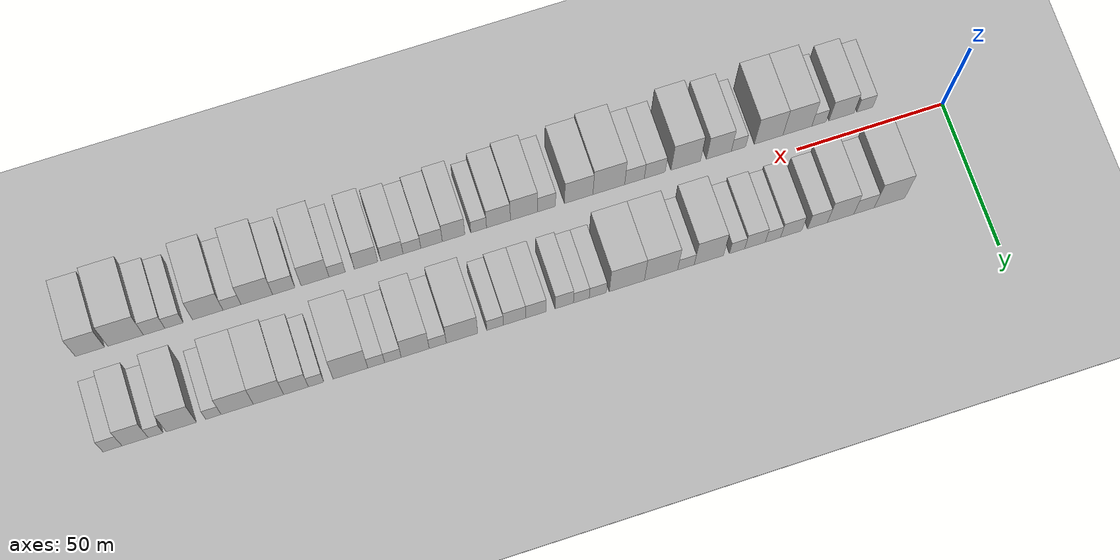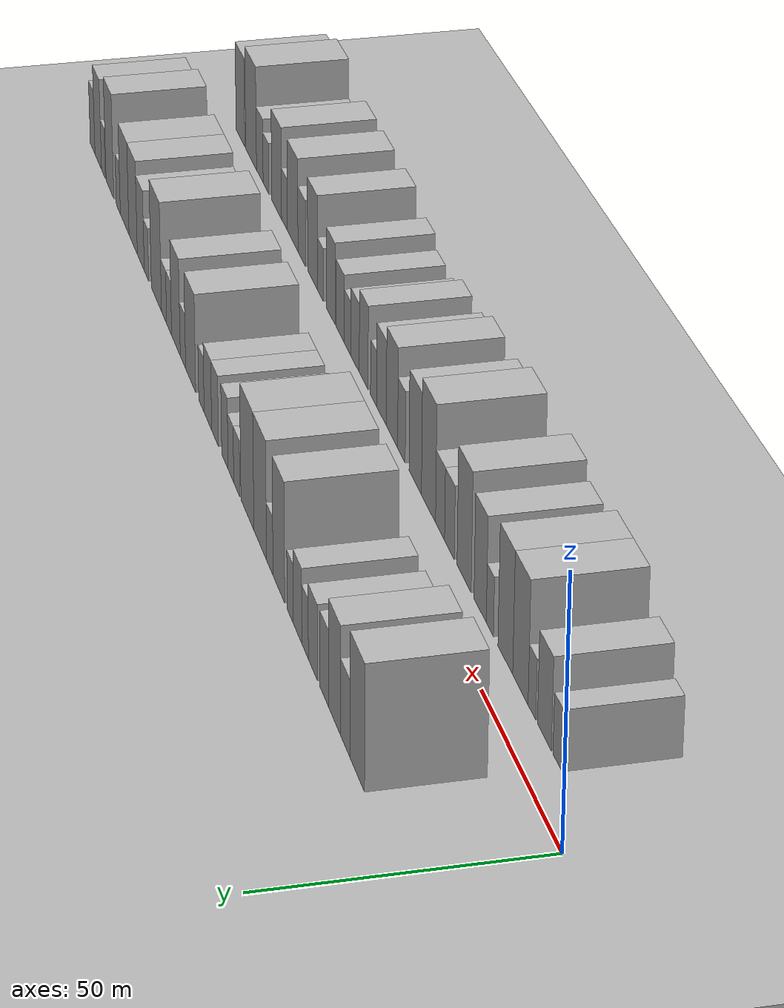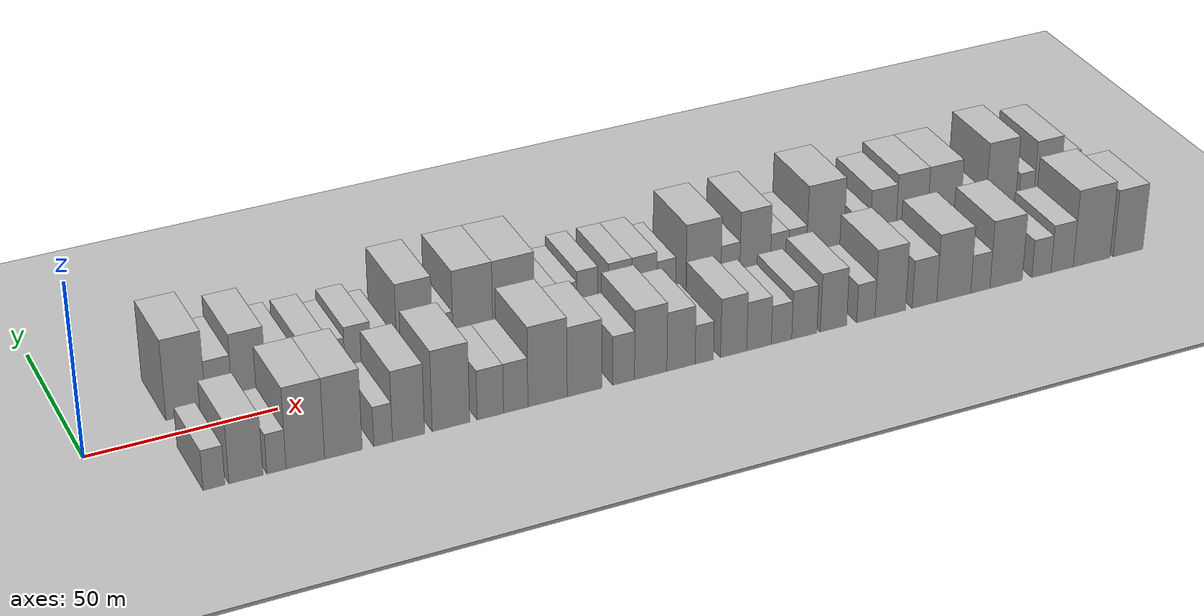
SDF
<?xml version="1.0" encoding="utf-8"?>

<sdf version="1.6">

   <world name="default">

      <gui fullscreen="0">

         <camera name="user_camera">

            <pose>-15 0 4.57585 0 0 0</pose>

            <view_controller>orbit</view_controller>

         </camera>

      </gui>

      <scene>

         <sky>

           <clouds>

             <speed>12</speed>

           </clouds>

         </sky>

         <ambient>0.4 0.4 0.4 1</ambient>

         <background>0.7 0.7 0.7 1</background>

         <shadows>1</shadows>

      </scene>

      <gravity>0 0 -9.8066</gravity>

      <magnetic_field>6e-06 2.3e-05 -4.2e-05</magnetic_field>

      <physics default="0" name="default_physics" type="ode">

         <ode>

            <solver>

               <type>quick</type>

               <iters>10</iters>

               <sor>1.0</sor>

               <use_dynamic_moi_rescaling>0</use_dynamic_moi_rescaling>

            </solver>

            <constraints>

               <cfm>0</cfm>

               <erp>0.2</erp>

               <contact_max_correcting_vel>100</contact_max_correcting_vel>

               <contact_surface_layer>0.001</contact_surface_layer>

            </constraints>

         </ode>

         <max_step_size>0.004</max_step_size>

         <real_time_factor>1</real_time_factor>

         <real_time_update_rate>250</real_time_update_rate>

      </physics>

      <light name="sun" type="directional">

         <cast_shadows>1</cast_shadows>

         <pose>0 0 10 0 0 0</pose>

         <diffuse>0.8 0.8 0.8 1</diffuse>

         <specular>0.2 0.2 0.2 1</specular>

         <attenuation>

            <range>1000</range>

            <constant>0.9</constant>

            <linear>0.01</linear>

            <quadratic>0.001</quadratic>

         </attenuation>

         <direction>-0.5 0.1 -0.9</direction>

      </light>

      <include>

         <name>ground_plane_1</name>

         <uri>model://HANNAS_ground_plane</uri>

         <pose>0 0 0  0 0 0</pose>

      </include>

      <include>

         <name>ground_plane_2</name>

         <uri>model://HANNAS_ground_plane</uri>

         <pose>100 0 0  0 0 0</pose>

      </include>

      <model name="building_1">

         <static>1</static>

         <pose frame="">28.2035 16.0000 0 0.000000 0.000000 1.570796</pose>

         <link name="link">

            <pose frame="">0 0 12.00 0 0 0</pose>

            <collision name="collision">

               <geometry>

                  <box>

                     <size>20.0000 10.4070 24.0000</size>

                  </box>

               </geometry>

               <max_contacts>10</max_contacts>

               <surface>

                  <contact>

                     <ode/>

                  </contact>

                  <bounce/>

                  <friction>

                     <torsional>

                        <ode/>

                     </torsional>

                     <ode/>

                  </friction>

               </surface>

            </collision>

            <visual name="visual">

               <cast_shadows>0</cast_shadows>

               <geometry>

                  <box>

                     <size>20.0000 10.4070 24.0000</size>

                  </box>

               </geometry>

               <material>

                  <script>

                     <uri>model://HANNAS_wall/materials/scripts</uri>

                     <uri>model://HANNAS_wall/materials/textures</uri>

                     <name>vrc/HANNAS_wall</name>

                  </script>

               </material>

            </visual>

            <self_collide>0</self_collide>

            <enable_wind>0</enable_wind>

            <kinematic>0</kinematic>

         </link>

      </model>

      <model name="building_2">

         <static>1</static>

         <pose frame="">36.8706 16.0000 0 0.000000 0.000000 1.570796</pose>

         <link name="link">

            <pose frame="">0 0 7.50 0 0 0</pose>

            <collision name="collision">

               <geometry>

                  <box>

                     <size>20.0000 6.9271 15.0000</size>

                  </box>

               </geometry>

               <max_contacts>10</max_contacts>

               <surface>

                  <contact>

                     <ode/>

                  </contact>

                  <bounce/>

                  <friction>

                     <torsional>

                        <ode/>

                     </torsional>

                     <ode/>

                  </friction>

               </surface>

            </collision>

            <visual name="visual">

               <cast_shadows>0</cast_shadows>

               <geometry>

                  <box>

                     <size>20.0000 6.9271 15.0000</size>

                  </box>

               </geometry>

               <material>

                  <script>

                     <uri>model://HANNAS_wall/materials/scripts</uri>

                     <uri>model://HANNAS_wall/materials/textures</uri>

                     <name>vrc/HANNAS_wall</name>

                  </script>

               </material>

            </visual>

            <self_collide>0</self_collide>

            <enable_wind>0</enable_wind>

            <kinematic>0</kinematic>

         </link>

      </model>

      <model name="building_3">

         <static>1</static>

         <pose frame="">44.8318 16.0000 0 0.000000 0.000000 1.570796</pose>

         <link name="link">

            <pose frame="">0 0 10.50 0 0 0</pose>

            <collision name="collision">

               <geometry>

                  <box>

                     <size>20.0000 8.9954 21.0000</size>

                  </box>

               </geometry>

               <max_contacts>10</max_contacts>

               <surface>

                  <contact>

                     <ode/>

                  </contact>

                  <bounce/>

                  <friction>

                     <torsional>

                        <ode/>

                     </torsional>

                     <ode/>

                  </friction>

               </surface>

            </collision>

            <visual name="visual">

               <cast_shadows>0</cast_shadows>

               <geometry>

                  <box>

                     <size>20.0000 8.9954 21.0000</size>

                  </box>

               </geometry>

               <material>

                  <script>

                     <uri>model://HANNAS_wall/materials/scripts</uri>

                     <uri>model://HANNAS_wall/materials/textures</uri>

                     <name>vrc/HANNAS_wall</name>

                  </script>

               </material>

            </visual>

            <self_collide>0</self_collide>

            <enable_wind>0</enable_wind>

            <kinematic>0</kinematic>

         </link>

      </model>

      <model name="building_4">

         <static>1</static>

         <pose frame="">52.6626 16.0000 0 0.000000 0.000000 1.570796</pose>

         <link name="link">

            <pose frame="">0 0 7.50 0 0 0</pose>

            <collision name="collision">

               <geometry>

                  <box>

                     <size>20.0000 6.6663 15.0000</size>

                  </box>

               </geometry>

               <max_contacts>10</max_contacts>

               <surface>

                  <contact>

                     <ode/>

                  </contact>

                  <bounce/>

                  <friction>

                     <torsional>

                        <ode/>

                     </torsional>

                     <ode/>

                  </friction>

               </surface>

            </collision>

            <visual name="visual">

               <cast_shadows>0</cast_shadows>

               <geometry>

                  <box>

                     <size>20.0000 6.6663 15.0000</size>

                  </box>

               </geometry>

               <material>

                  <script>

                     <uri>model://HANNAS_wall/materials/scripts</uri>

                     <uri>model://HANNAS_wall/materials/textures</uri>

                     <name>vrc/HANNAS_wall</name>

                  </script>

               </material>

            </visual>

            <self_collide>0</self_collide>

            <enable_wind>0</enable_wind>

            <kinematic>0</kinematic>

         </link>

      </model>

      <model name="building_5">

         <static>1</static>

         <pose frame="">61.5782 16.0000 0 0.000000 0.000000 1.570796</pose>

         <link name="link">

            <pose frame="">0 0 7.50 0 0 0</pose>

            <collision name="collision">

               <geometry>

                  <box>

                     <size>20.0000 7.1649 15.0000</size>

                  </box>

               </geometry>

               <max_contacts>10</max_contacts>

               <surface>

                  <contact>

                     <ode/>

                  </contact>

                  <bounce/>

                  <friction>

                     <torsional>

                        <ode/>

                     </torsional>

                     <ode/>

                  </friction>

               </surface>

            </collision>

            <visual name="visual">

               <cast_shadows>0</cast_shadows>

               <geometry>

                  <box>

                     <size>20.0000 7.1649 15.0000</size>

                  </box>

               </geometry>

               <material>

                  <script>

                     <uri>model://HANNAS_wall/materials/scripts</uri>

                     <uri>model://HANNAS_wall/materials/textures</uri>

                     <name>vrc/HANNAS_wall</name>

                  </script>

               </material>

            </visual>

            <self_collide>0</self_collide>

            <enable_wind>0</enable_wind>

            <kinematic>0</kinematic>

         </link>

      </model>

      <model name="building_6">

         <static>1</static>

         <pose frame="">67.7352 16.0000 0 0.000000 0.000000 1.570796</pose>

         <link name="link">

            <pose frame="">0 0 6.00 0 0 0</pose>

            <collision name="collision">

               <geometry>

                  <box>

                     <size>20.0000 5.1490 12.0000</size>

                  </box>

               </geometry>

               <max_contacts>10</max_contacts>

               <surface>

                  <contact>

                     <ode/>

                  </contact>

                  <bounce/>

                  <friction>

                     <torsional>

                        <ode/>

                     </torsional>

                     <ode/>

                  </friction>

               </surface>

            </collision>

            <visual name="visual">

               <cast_shadows>0</cast_shadows>

               <geometry>

                  <box>

                     <size>20.0000 5.1490 12.0000</size>

                  </box>

               </geometry>

               <material>

                  <script>

                     <uri>model://HANNAS_wall/materials/scripts</uri>

                     <uri>model://HANNAS_wall/materials/textures</uri>

                     <name>vrc/HANNAS_wall</name>

                  </script>

               </material>

            </visual>

            <self_collide>0</self_collide>

            <enable_wind>0</enable_wind>

            <kinematic>0</kinematic>

         </link>

      </model>

      <model name="building_7">

         <static>1</static>

         <pose frame="">73.7785 16.0000 0 0.000000 0.000000 1.570796</pose>

         <link name="link">

            <pose frame="">0 0 7.50 0 0 0</pose>

            <collision name="collision">

               <geometry>

                  <box>

                     <size>20.0000 6.9376 15.0000</size>

                  </box>

               </geometry>

               <max_contacts>10</max_contacts>

               <surface>

                  <contact>

                     <ode/>

                  </contact>

                  <bounce/>

                  <friction>

                     <torsional>

                        <ode/>

                     </torsional>

                     <ode/>

                  </friction>

               </surface>

            </collision>

            <visual name="visual">

               <cast_shadows>0</cast_shadows>

               <geometry>

                  <box>

                     <size>20.0000 6.9376 15.0000</size>

                  </box>

               </geometry>

               <material>

                  <script>

                     <uri>model://HANNAS_wall/materials/scripts</uri>

                     <uri>model://HANNAS_wall/materials/textures</uri>

                     <name>vrc/HANNAS_wall</name>

                  </script>

               </material>

            </visual>

            <self_collide>0</self_collide>

            <enable_wind>0</enable_wind>

            <kinematic>0</kinematic>

         </link>

      </model>

      <model name="building_8">

         <static>1</static>

         <pose frame="">79.8023 16.0000 0 0.000000 0.000000 1.570796</pose>

         <link name="link">

            <pose frame="">0 0 6.00 0 0 0</pose>

            <collision name="collision">

               <geometry>

                  <box>

                     <size>20.0000 5.1100 12.0000</size>

                  </box>

               </geometry>

               <max_contacts>10</max_contacts>

               <surface>

                  <contact>

                     <ode/>

                  </contact>

                  <bounce/>

                  <friction>

                     <torsional>

                        <ode/>

                     </torsional>

                     <ode/>

                  </friction>

               </surface>

            </collision>

            <visual name="visual">

               <cast_shadows>0</cast_shadows>

               <geometry>

                  <box>

                     <size>20.0000 5.1100 12.0000</size>

                  </box>

               </geometry>

               <material>

                  <script>

                     <uri>model://HANNAS_wall/materials/scripts</uri>

                     <uri>model://HANNAS_wall/materials/textures</uri>

                     <name>vrc/HANNAS_wall</name>

                  </script>

               </material>

            </visual>

            <self_collide>0</self_collide>

            <enable_wind>0</enable_wind>

            <kinematic>0</kinematic>

         </link>

      </model>

      <model name="building_9">

         <static>1</static>

         <pose frame="">89.2680 16.0000 0 0.000000 0.000000 1.570796</pose>

         <link name="link">

            <pose frame="">0 0 12.00 0 0 0</pose>

            <collision name="collision">

               <geometry>

                  <box>

                     <size>20.0000 9.8214 24.0000</size>

                  </box>

               </geometry>

               <max_contacts>10</max_contacts>

               <surface>

                  <contact>

                     <ode/>

                  </contact>

                  <bounce/>

                  <friction>

                     <torsional>

                        <ode/>

                     </torsional>

                     <ode/>

                  </friction>

               </surface>

            </collision>

            <visual name="visual">

               <cast_shadows>0</cast_shadows>

               <geometry>

                  <box>

                     <size>20.0000 9.8214 24.0000</size>

                  </box>

               </geometry>

               <material>

                  <script>

                     <uri>model://HANNAS_wall/materials/scripts</uri>

                     <uri>model://HANNAS_wall/materials/textures</uri>

                     <name>vrc/HANNAS_wall</name>

                  </script>

               </material>

            </visual>

            <self_collide>0</self_collide>

            <enable_wind>0</enable_wind>

            <kinematic>0</kinematic>

         </link>

      </model>

      <model name="building_10">

         <static>1</static>

         <pose frame="">96.9650 16.0000 0 0.000000 0.000000 1.570796</pose>

         <link name="link">

            <pose frame="">0 0 6.00 0 0 0</pose>

            <collision name="collision">

               <geometry>

                  <box>

                     <size>20.0000 5.5726 12.0000</size>

                  </box>

               </geometry>

               <max_contacts>10</max_contacts>

               <surface>

                  <contact>

                     <ode/>

                  </contact>

                  <bounce/>

                  <friction>

                     <torsional>

                        <ode/>

                     </torsional>

                     <ode/>

                  </friction>

               </surface>

            </collision>

            <visual name="visual">

               <cast_shadows>0</cast_shadows>

               <geometry>

                  <box>

                     <size>20.0000 5.5726 12.0000</size>

                  </box>

               </geometry>

               <material>

                  <script>

                     <uri>model://HANNAS_wall/materials/scripts</uri>

                     <uri>model://HANNAS_wall/materials/textures</uri>

                     <name>vrc/HANNAS_wall</name>

                  </script>

               </material>

            </visual>

            <self_collide>0</self_collide>

            <enable_wind>0</enable_wind>

            <kinematic>0</kinematic>

         </link>

      </model>

      <model name="building_11">

         <static>1</static>

         <pose frame="">105.2956 16.0000 0 0.000000 0.000000 1.570796</pose>

         <link name="link">

            <pose frame="">0 0 12.00 0 0 0</pose>

            <collision name="collision">

               <geometry>

                  <box>

                     <size>20.0000 11.0885 24.0000</size>

                  </box>

               </geometry>

               <max_contacts>10</max_contacts>

               <surface>

                  <contact>

                     <ode/>

                  </contact>

                  <bounce/>

                  <friction>

                     <torsional>

                        <ode/>

                     </torsional>

                     <ode/>

                  </friction>

               </surface>

            </collision>

            <visual name="visual">

               <cast_shadows>0</cast_shadows>

               <geometry>

                  <box>

                     <size>20.0000 11.0885 24.0000</size>

                  </box>

               </geometry>

               <material>

                  <script>

                     <uri>model://HANNAS_wall/materials/scripts</uri>

                     <uri>model://HANNAS_wall/materials/textures</uri>

                     <name>vrc/HANNAS_wall</name>

                  </script>

               </material>

            </visual>

            <self_collide>0</self_collide>

            <enable_wind>0</enable_wind>

            <kinematic>0</kinematic>

         </link>

      </model>

      <model name="building_12">

         <static>1</static>

         <pose frame="">116.6909 16.0000 0 0.000000 0.000000 1.570796</pose>

         <link name="link">

            <pose frame="">0 0 12.00 0 0 0</pose>

            <collision name="collision">

               <geometry>

                  <box>

                     <size>20.0000 11.7021 24.0000</size>

                  </box>

               </geometry>

               <max_contacts>10</max_contacts>

               <surface>

                  <contact>

                     <ode/>

                  </contact>

                  <bounce/>

                  <friction>

                     <torsional>

                        <ode/>

                     </torsional>

                     <ode/>

                  </friction>

               </surface>

            </collision>

            <visual name="visual">

               <cast_shadows>0</cast_shadows>

               <geometry>

                  <box>

                     <size>20.0000 11.7021 24.0000</size>

                  </box>

               </geometry>

               <material>

                  <script>

                     <uri>model://HANNAS_wall/materials/scripts</uri>

                     <uri>model://HANNAS_wall/materials/textures</uri>

                     <name>vrc/HANNAS_wall</name>

                  </script>

               </material>

            </visual>

            <self_collide>0</self_collide>

            <enable_wind>0</enable_wind>

            <kinematic>0</kinematic>

         </link>

      </model>

      <model name="building_13">

         <static>1</static>

         <pose frame="">126.3763 16.0000 0 0.000000 0.000000 1.570796</pose>

         <link name="link">

            <pose frame="">0 0 6.00 0 0 0</pose>

            <collision name="collision">

               <geometry>

                  <box>

                     <size>20.0000 5.6688 12.0000</size>

                  </box>

               </geometry>

               <max_contacts>10</max_contacts>

               <surface>

                  <contact>

                     <ode/>

                  </contact>

                  <bounce/>

                  <friction>

                     <torsional>

                        <ode/>

                     </torsional>

                     <ode/>

                  </friction>

               </surface>

            </collision>

            <visual name="visual">

               <cast_shadows>0</cast_shadows>

               <geometry>

                  <box>

                     <size>20.0000 5.6688 12.0000</size>

                  </box>

               </geometry>

               <material>

                  <script>

                     <uri>model://HANNAS_wall/materials/scripts</uri>

                     <uri>model://HANNAS_wall/materials/textures</uri>

                     <name>vrc/HANNAS_wall</name>

                  </script>

               </material>

            </visual>

            <self_collide>0</self_collide>

            <enable_wind>0</enable_wind>

            <kinematic>0</kinematic>

         </link>

      </model>

      <model name="building_14">

         <static>1</static>

         <pose frame="">131.8402 16.0000 0 0.000000 0.000000 1.570796</pose>

         <link name="link">

            <pose frame="">0 0 6.00 0 0 0</pose>

            <collision name="collision">

               <geometry>

                  <box>

                     <size>20.0000 5.2590 12.0000</size>

                  </box>

               </geometry>

               <max_contacts>10</max_contacts>

               <surface>

                  <contact>

                     <ode/>

                  </contact>

                  <bounce/>

                  <friction>

                     <torsional>

                        <ode/>

                     </torsional>

                     <ode/>

                  </friction>

               </surface>

            </collision>

            <visual name="visual">

               <cast_shadows>0</cast_shadows>

               <geometry>

                  <box>

                     <size>20.0000 5.2590 12.0000</size>

                  </box>

               </geometry>

               <material>

                  <script>

                     <uri>model://HANNAS_wall/materials/scripts</uri>

                     <uri>model://HANNAS_wall/materials/textures</uri>

                     <name>vrc/HANNAS_wall</name>

                  </script>

               </material>

            </visual>

            <self_collide>0</self_collide>

            <enable_wind>0</enable_wind>

            <kinematic>0</kinematic>

         </link>

      </model>

      <model name="building_15">

         <static>1</static>

         <pose frame="">137.5098 16.0000 0 0.000000 0.000000 1.570796</pose>

         <link name="link">

            <pose frame="">0 0 7.50 0 0 0</pose>

            <collision name="collision">

               <geometry>

                  <box>

                     <size>20.0000 6.0801 15.0000</size>

                  </box>

               </geometry>

               <max_contacts>10</max_contacts>

               <surface>

                  <contact>

                     <ode/>

                  </contact>

                  <bounce/>

                  <friction>

                     <torsional>

                        <ode/>

                     </torsional>

                     <ode/>

                  </friction>

               </surface>

            </collision>

            <visual name="visual">

               <cast_shadows>0</cast_shadows>

               <geometry>

                  <box>

                     <size>20.0000 6.0801 15.0000</size>

                  </box>

               </geometry>

               <material>

                  <script>

                     <uri>model://HANNAS_wall/materials/scripts</uri>

                     <uri>model://HANNAS_wall/materials/textures</uri>

                     <name>vrc/HANNAS_wall</name>

                  </script>

               </material>

            </visual>

            <self_collide>0</self_collide>

            <enable_wind>0</enable_wind>

            <kinematic>0</kinematic>

         </link>

      </model>

      <model name="building_16">

         <static>1</static>

         <pose frame="">146.9036 16.0000 0 0.000000 0.000000 1.570796</pose>

         <link name="link">

            <pose frame="">0 0 7.50 0 0 0</pose>

            <collision name="collision">

               <geometry>

                  <box>

                     <size>20.0000 6.7075 15.0000</size>

                  </box>

               </geometry>

               <max_contacts>10</max_contacts>

               <surface>

                  <contact>

                     <ode/>

                  </contact>

                  <bounce/>

                  <friction>

                     <torsional>

                        <ode/>

                     </torsional>

                     <ode/>

                  </friction>

               </surface>

            </collision>

            <visual name="visual">

               <cast_shadows>0</cast_shadows>

               <geometry>

                  <box>

                     <size>20.0000 6.7075 15.0000</size>

                  </box>

               </geometry>

               <material>

                  <script>

                     <uri>model://HANNAS_wall/materials/scripts</uri>

                     <uri>model://HANNAS_wall/materials/textures</uri>

                     <name>vrc/HANNAS_wall</name>

                  </script>

               </material>

            </visual>

            <self_collide>0</self_collide>

            <enable_wind>0</enable_wind>

            <kinematic>0</kinematic>

         </link>

      </model>

      <model name="building_17">

         <static>1</static>

         <pose frame="">153.9549 16.0000 0 0.000000 0.000000 1.570796</pose>

         <link name="link">

            <pose frame="">0 0 7.50 0 0 0</pose>

            <collision name="collision">

               <geometry>

                  <box>

                     <size>20.0000 7.3951 15.0000</size>

                  </box>

               </geometry>

               <max_contacts>10</max_contacts>

               <surface>

                  <contact>

                     <ode/>

                  </contact>

                  <bounce/>

                  <friction>

                     <torsional>

                        <ode/>

                     </torsional>

                     <ode/>

                  </friction>

               </surface>

            </collision>

            <visual name="visual">

               <cast_shadows>0</cast_shadows>

               <geometry>

                  <box>

                     <size>20.0000 7.3951 15.0000</size>

                  </box>

               </geometry>

               <material>

                  <script>

                     <uri>model://HANNAS_wall/materials/scripts</uri>

                     <uri>model://HANNAS_wall/materials/textures</uri>

                     <name>vrc/HANNAS_wall</name>

                  </script>

               </material>

            </visual>

            <self_collide>0</self_collide>

            <enable_wind>0</enable_wind>

            <kinematic>0</kinematic>

         </link>

      </model>

      <model name="building_18">

         <static>1</static>

         <pose frame="">160.3797 16.0000 0 0.000000 0.000000 1.570796</pose>

         <link name="link">

            <pose frame="">0 0 6.00 0 0 0</pose>

            <collision name="collision">

               <geometry>

                  <box>

                     <size>20.0000 5.4544 12.0000</size>

                  </box>

               </geometry>

               <max_contacts>10</max_contacts>

               <surface>

                  <contact>

                     <ode/>

                  </contact>

                  <bounce/>

                  <friction>

                     <torsional>

                        <ode/>

                     </torsional>

                     <ode/>

                  </friction>

               </surface>

            </collision>

            <visual name="visual">

               <cast_shadows>0</cast_shadows>

               <geometry>

                  <box>

                     <size>20.0000 5.4544 12.0000</size>

                  </box>

               </geometry>

               <material>

                  <script>

                     <uri>model://HANNAS_wall/materials/scripts</uri>

                     <uri>model://HANNAS_wall/materials/textures</uri>

                     <name>vrc/HANNAS_wall</name>

                  </script>

               </material>

            </visual>

            <self_collide>0</self_collide>

            <enable_wind>0</enable_wind>

            <kinematic>0</kinematic>

         </link>

      </model>

      <model name="building_19">

         <static>1</static>

         <pose frame="">171.2821 16.0000 0 0.000000 0.000000 1.570796</pose>

         <link name="link">

            <pose frame="">0 0 10.50 0 0 0</pose>

            <collision name="collision">

               <geometry>

                  <box>

                     <size>20.0000 10.3504 21.0000</size>

                  </box>

               </geometry>

               <max_contacts>10</max_contacts>

               <surface>

                  <contact>

                     <ode/>

                  </contact>

                  <bounce/>

                  <friction>

                     <torsional>

                        <ode/>

                     </torsional>

                     <ode/>

                  </friction>

               </surface>

            </collision>

            <visual name="visual">

               <cast_shadows>0</cast_shadows>

               <geometry>

                  <box>

                     <size>20.0000 10.3504 21.0000</size>

                  </box>

               </geometry>

               <material>

                  <script>

                     <uri>model://HANNAS_wall/materials/scripts</uri>

                     <uri>model://HANNAS_wall/materials/textures</uri>

                     <name>vrc/HANNAS_wall</name>

                  </script>

               </material>

            </visual>

            <self_collide>0</self_collide>

            <enable_wind>0</enable_wind>

            <kinematic>0</kinematic>

         </link>

      </model>

      <model name="building_20">

         <static>1</static>

         <pose frame="">179.2618 16.0000 0 0.000000 0.000000 1.570796</pose>

         <link name="link">

            <pose frame="">0 0 6.00 0 0 0</pose>

            <collision name="collision">

               <geometry>

                  <box>

                     <size>20.0000 5.6091 12.0000</size>

                  </box>

               </geometry>

               <max_contacts>10</max_contacts>

               <surface>

                  <contact>

                     <ode/>

                  </contact>

                  <bounce/>

                  <friction>

                     <torsional>

                        <ode/>

                     </torsional>

                     <ode/>

                  </friction>

               </surface>

            </collision>

            <visual name="visual">

               <cast_shadows>0</cast_shadows>

               <geometry>

                  <box>

                     <size>20.0000 5.6091 12.0000</size>

                  </box>

               </geometry>

               <material>

                  <script>

                     <uri>model://HANNAS_wall/materials/scripts</uri>

                     <uri>model://HANNAS_wall/materials/textures</uri>

                     <name>vrc/HANNAS_wall</name>

                  </script>

               </material>

            </visual>

            <self_collide>0</self_collide>

            <enable_wind>0</enable_wind>

            <kinematic>0</kinematic>

         </link>

      </model>

      <model name="building_21">

         <static>1</static>

         <pose frame="">186.6494 16.0000 0 0.000000 0.000000 1.570796</pose>

         <link name="link">

            <pose frame="">0 0 10.50 0 0 0</pose>

            <collision name="collision">

               <geometry>

                  <box>

                     <size>20.0000 9.1661 21.0000</size>

                  </box>

               </geometry>

               <max_contacts>10</max_contacts>

               <surface>

                  <contact>

                     <ode/>

                  </contact>

                  <bounce/>

                  <friction>

                     <torsional>

                        <ode/>

                     </torsional>

                     <ode/>

                  </friction>

               </surface>

            </collision>

            <visual name="visual">

               <cast_shadows>0</cast_shadows>

               <geometry>

                  <box>

                     <size>20.0000 9.1661 21.0000</size>

                  </box>

               </geometry>

               <material>

                  <script>

                     <uri>model://HANNAS_wall/materials/scripts</uri>

                     <uri>model://HANNAS_wall/materials/textures</uri>

                     <name>vrc/HANNAS_wall</name>

                  </script>

               </material>

            </visual>

            <self_collide>0</self_collide>

            <enable_wind>0</enable_wind>

            <kinematic>0</kinematic>

         </link>

      </model>

      <model name="building_22">

         <static>1</static>

         <pose frame="">193.9422 16.0000 0 0.000000 0.000000 1.570796</pose>

         <link name="link">

            <pose frame="">0 0 6.00 0 0 0</pose>

            <collision name="collision">

               <geometry>

                  <box>

                     <size>20.0000 5.4194 12.0000</size>

                  </box>

               </geometry>

               <max_contacts>10</max_contacts>

               <surface>

                  <contact>

                     <ode/>

                  </contact>

                  <bounce/>

                  <friction>

                     <torsional>

                        <ode/>

                     </torsional>

                     <ode/>

                  </friction>

               </surface>

            </collision>

            <visual name="visual">

               <cast_shadows>0</cast_shadows>

               <geometry>

                  <box>

                     <size>20.0000 5.4194 12.0000</size>

                  </box>

               </geometry>

               <material>

                  <script>

                     <uri>model://HANNAS_wall/materials/scripts</uri>

                     <uri>model://HANNAS_wall/materials/textures</uri>

                     <name>vrc/HANNAS_wall</name>

                  </script>

               </material>

            </visual>

            <self_collide>0</self_collide>

            <enable_wind>0</enable_wind>

            <kinematic>0</kinematic>

         </link>

      </model>

      <model name="building_23">

         <static>1</static>

         <pose frame="">199.4075 16.0000 0 0.000000 0.000000 1.570796</pose>

         <link name="link">

            <pose frame="">0 0 6.00 0 0 0</pose>

            <collision name="collision">

               <geometry>

                  <box>

                     <size>20.0000 5.5114 12.0000</size>

                  </box>

               </geometry>

               <max_contacts>10</max_contacts>

               <surface>

                  <contact>

                     <ode/>

                  </contact>

                  <bounce/>

                  <friction>

                     <torsional>

                        <ode/>

                     </torsional>

                     <ode/>

                  </friction>

               </surface>

            </collision>

            <visual name="visual">

               <cast_shadows>0</cast_shadows>

               <geometry>

                  <box>

                     <size>20.0000 5.5114 12.0000</size>

                  </box>

               </geometry>

               <material>

                  <script>

                     <uri>model://HANNAS_wall/materials/scripts</uri>

                     <uri>model://HANNAS_wall/materials/textures</uri>

                     <name>vrc/HANNAS_wall</name>

                  </script>

               </material>

            </visual>

            <self_collide>0</self_collide>

            <enable_wind>0</enable_wind>

            <kinematic>0</kinematic>

         </link>

      </model>

      <model name="building_24">

         <static>1</static>

         <pose frame="">207.8202 16.0000 0 0.000000 0.000000 1.570796</pose>

         <link name="link">

            <pose frame="">0 0 12.00 0 0 0</pose>

            <collision name="collision">

               <geometry>

                  <box>

                     <size>20.0000 11.3139 24.0000</size>

                  </box>

               </geometry>

               <max_contacts>10</max_contacts>

               <surface>

                  <contact>

                     <ode/>

                  </contact>

                  <bounce/>

                  <friction>

                     <torsional>

                        <ode/>

                     </torsional>

                     <ode/>

                  </friction>

               </surface>

            </collision>

            <visual name="visual">

               <cast_shadows>0</cast_shadows>

               <geometry>

                  <box>

                     <size>20.0000 11.3139 24.0000</size>

                  </box>

               </geometry>

               <material>

                  <script>

                     <uri>model://HANNAS_wall/materials/scripts</uri>

                     <uri>model://HANNAS_wall/materials/textures</uri>

                     <name>vrc/HANNAS_wall</name>

                  </script>

               </material>

            </visual>

            <self_collide>0</self_collide>

            <enable_wind>0</enable_wind>

            <kinematic>0</kinematic>

         </link>

      </model>

      <model name="building_25">

         <static>1</static>

         <pose frame="">219.0032 16.0000 0 0.000000 0.000000 1.570796</pose>

         <link name="link">

            <pose frame="">0 0 6.00 0 0 0</pose>

            <collision name="collision">

               <geometry>

                  <box>

                     <size>20.0000 5.0522 12.0000</size>

                  </box>

               </geometry>

               <max_contacts>10</max_contacts>

               <surface>

                  <contact>

                     <ode/>

                  </contact>

                  <bounce/>

                  <friction>

                     <torsional>

                        <ode/>

                     </torsional>

                     <ode/>

                  </friction>

               </surface>

            </collision>

            <visual name="visual">

               <cast_shadows>0</cast_shadows>

               <geometry>

                  <box>

                     <size>20.0000 5.0522 12.0000</size>

                  </box>

               </geometry>

               <material>

                  <script>

                     <uri>model://HANNAS_wall/materials/scripts</uri>

                     <uri>model://HANNAS_wall/materials/textures</uri>

                     <name>vrc/HANNAS_wall</name>

                  </script>

               </material>

            </visual>

            <self_collide>0</self_collide>

            <enable_wind>0</enable_wind>

            <kinematic>0</kinematic>

         </link>

      </model>

      <model name="building_26">

         <static>1</static>

         <pose frame="">225.5476 16.0000 0 0.000000 0.000000 1.570796</pose>

         <link name="link">

            <pose frame="">0 0 9.00 0 0 0</pose>

            <collision name="collision">

               <geometry>

                  <box>

                     <size>20.0000 8.0365 18.0000</size>

                  </box>

               </geometry>

               <max_contacts>10</max_contacts>

               <surface>

                  <contact>

                     <ode/>

                  </contact>

                  <bounce/>

                  <friction>

                     <torsional>

                        <ode/>

                     </torsional>

                     <ode/>

                  </friction>

               </surface>

            </collision>

            <visual name="visual">

               <cast_shadows>0</cast_shadows>

               <geometry>

                  <box>

                     <size>20.0000 8.0365 18.0000</size>

                  </box>

               </geometry>

               <material>

                  <script>

                     <uri>model://HANNAS_wall/materials/scripts</uri>

                     <uri>model://HANNAS_wall/materials/textures</uri>

                     <name>vrc/HANNAS_wall</name>

                  </script>

               </material>

            </visual>

            <self_collide>0</self_collide>

            <enable_wind>0</enable_wind>

            <kinematic>0</kinematic>

         </link>

      </model>

      <model name="building_27">

         <static>1</static>

         <pose frame="">234.4667 16.0000 0 0.000000 0.000000 1.570796</pose>

         <link name="link">

            <pose frame="">0 0 10.50 0 0 0</pose>

            <collision name="collision">

               <geometry>

                  <box>

                     <size>20.0000 9.8018 21.0000</size>

                  </box>

               </geometry>

               <max_contacts>10</max_contacts>

               <surface>

                  <contact>

                     <ode/>

                  </contact>

                  <bounce/>

                  <friction>

                     <torsional>

                        <ode/>

                     </torsional>

                     <ode/>

                  </friction>

               </surface>

            </collision>

            <visual name="visual">

               <cast_shadows>0</cast_shadows>

               <geometry>

                  <box>

                     <size>20.0000 9.8018 21.0000</size>

                  </box>

               </geometry>

               <material>

                  <script>

                     <uri>model://HANNAS_wall/materials/scripts</uri>

                     <uri>model://HANNAS_wall/materials/textures</uri>

                     <name>vrc/HANNAS_wall</name>

                  </script>

               </material>

            </visual>

            <self_collide>0</self_collide>

            <enable_wind>0</enable_wind>

            <kinematic>0</kinematic>

         </link>

      </model>

      <model name="building_28">

         <static>1</static>

         <pose frame="">244.5770 16.0000 0 0.000000 0.000000 1.570796</pose>

         <link name="link">

            <pose frame="">0 0 10.50 0 0 0</pose>

            <collision name="collision">

               <geometry>

                  <box>

                     <size>20.0000 10.4188 21.0000</size>

                  </box>

               </geometry>

               <max_contacts>10</max_contacts>

               <surface>

                  <contact>

                     <ode/>

                  </contact>

                  <bounce/>

                  <friction>

                     <torsional>

                        <ode/>

                     </torsional>

                     <ode/>

                  </friction>

               </surface>

            </collision>

            <visual name="visual">

               <cast_shadows>0</cast_shadows>

               <geometry>

                  <box>

                     <size>20.0000 10.4188 21.0000</size>

                  </box>

               </geometry>

               <material>

                  <script>

                     <uri>model://HANNAS_wall/materials/scripts</uri>

                     <uri>model://HANNAS_wall/materials/textures</uri>

                     <name>vrc/HANNAS_wall</name>

                  </script>

               </material>

            </visual>

            <self_collide>0</self_collide>

            <enable_wind>0</enable_wind>

            <kinematic>0</kinematic>

         </link>

      </model>

      <model name="building_29">

         <static>1</static>

         <pose frame="">252.2715 16.0000 0 0.000000 0.000000 1.570796</pose>

         <link name="link">

            <pose frame="">0 0 6.00 0 0 0</pose>

            <collision name="collision">

               <geometry>

                  <box>

                     <size>20.0000 4.9702 12.0000</size>

                  </box>

               </geometry>

               <max_contacts>10</max_contacts>

               <surface>

                  <contact>

                     <ode/>

                  </contact>

                  <bounce/>

                  <friction>

                     <torsional>

                        <ode/>

                     </torsional>

                     <ode/>

                  </friction>

               </surface>

            </collision>

            <visual name="visual">

               <cast_shadows>0</cast_shadows>

               <geometry>

                  <box>

                     <size>20.0000 4.9702 12.0000</size>

                  </box>

               </geometry>

               <material>

                  <script>

                     <uri>model://HANNAS_wall/materials/scripts</uri>

                     <uri>model://HANNAS_wall/materials/textures</uri>

                     <name>vrc/HANNAS_wall</name>

                  </script>

               </material>

            </visual>

            <self_collide>0</self_collide>

            <enable_wind>0</enable_wind>

            <kinematic>0</kinematic>

         </link>

      </model>

      <model name="building_30">

         <static>1</static>

         <pose frame="">262.6057 16.0000 0 0.000000 0.000000 1.570796</pose>

         <link name="link">

            <pose frame="">0 0 12.00 0 0 0</pose>

            <collision name="collision">

               <geometry>

                  <box>

                     <size>20.0000 9.6982 24.0000</size>

                  </box>

               </geometry>

               <max_contacts>10</max_contacts>

               <surface>

                  <contact>

                     <ode/>

                  </contact>

                  <bounce/>

                  <friction>

                     <torsional>

                        <ode/>

                     </torsional>

                     <ode/>

                  </friction>

               </surface>

            </collision>

            <visual name="visual">

               <cast_shadows>0</cast_shadows>

               <geometry>

                  <box>

                     <size>20.0000 9.6982 24.0000</size>

                  </box>

               </geometry>

               <material>

                  <script>

                     <uri>model://HANNAS_wall/materials/scripts</uri>

                     <uri>model://HANNAS_wall/materials/textures</uri>

                     <name>vrc/HANNAS_wall</name>

                  </script>

               </material>

            </visual>

            <self_collide>0</self_collide>

            <enable_wind>0</enable_wind>

            <kinematic>0</kinematic>

         </link>

      </model>

      <model name="building_31">

         <static>1</static>

         <pose frame="">270.8627 16.0000 0 0.000000 0.000000 1.570796</pose>

         <link name="link">

            <pose frame="">0 0 6.00 0 0 0</pose>

            <collision name="collision">

               <geometry>

                  <box>

                     <size>20.0000 4.8157 12.0000</size>

                  </box>

               </geometry>

               <max_contacts>10</max_contacts>

               <surface>

                  <contact>

                     <ode/>

                  </contact>

                  <bounce/>

                  <friction>

                     <torsional>

                        <ode/>

                     </torsional>

                     <ode/>

                  </friction>

               </surface>

            </collision>

            <visual name="visual">

               <cast_shadows>0</cast_shadows>

               <geometry>

                  <box>

                     <size>20.0000 4.8157 12.0000</size>

                  </box>

               </geometry>

               <material>

                  <script>

                     <uri>model://HANNAS_wall/materials/scripts</uri>

                     <uri>model://HANNAS_wall/materials/textures</uri>

                     <name>vrc/HANNAS_wall</name>

                  </script>

               </material>

            </visual>

            <self_collide>0</self_collide>

            <enable_wind>0</enable_wind>

            <kinematic>0</kinematic>

         </link>

      </model>

      <model name="building_32">

         <static>1</static>

         <pose frame="">277.4708 16.0000 0 0.000000 0.000000 1.570796</pose>

         <link name="link">

            <pose frame="">0 0 10.50 0 0 0</pose>

            <collision name="collision">

               <geometry>

                  <box>

                     <size>20.0000 8.4004 21.0000</size>

                  </box>

               </geometry>

               <max_contacts>10</max_contacts>

               <surface>

                  <contact>

                     <ode/>

                  </contact>

                  <bounce/>

                  <friction>

                     <torsional>

                        <ode/>

                     </torsional>

                     <ode/>

                  </friction>

               </surface>

            </collision>

            <visual name="visual">

               <cast_shadows>0</cast_shadows>

               <geometry>

                  <box>

                     <size>20.0000 8.4004 21.0000</size>

                  </box>

               </geometry>

               <material>

                  <script>

                     <uri>model://HANNAS_wall/materials/scripts</uri>

                     <uri>model://HANNAS_wall/materials/textures</uri>

                     <name>vrc/HANNAS_wall</name>

                  </script>

               </material>

            </visual>

            <self_collide>0</self_collide>

            <enable_wind>0</enable_wind>

            <kinematic>0</kinematic>

         </link>

      </model>

      <model name="building_33">

         <static>1</static>

         <pose frame="">284.7169 16.0000 0 0.000000 0.000000 1.570796</pose>

         <link name="link">

            <pose frame="">0 0 7.50 0 0 0</pose>

            <collision name="collision">

               <geometry>

                  <box>

                     <size>20.0000 6.0919 15.0000</size>

                  </box>

               </geometry>

               <max_contacts>10</max_contacts>

               <surface>

                  <contact>

                     <ode/>

                  </contact>

                  <bounce/>

                  <friction>

                     <torsional>

                        <ode/>

                     </torsional>

                     <ode/>

                  </friction>

               </surface>

            </collision>

            <visual name="visual">

               <cast_shadows>0</cast_shadows>

               <geometry>

                  <box>

                     <size>20.0000 6.0919 15.0000</size>

                  </box>

               </geometry>

               <material>

                  <script>

                     <uri>model://HANNAS_wall/materials/scripts</uri>

                     <uri>model://HANNAS_wall/materials/textures</uri>

                     <name>vrc/HANNAS_wall</name>

                  </script>

               </material>

            </visual>

            <self_collide>0</self_collide>

            <enable_wind>0</enable_wind>

            <kinematic>0</kinematic>

         </link>

      </model>

      <model name="building_34">

         <static>1</static>

         <pose frame="">24.7283 -16.0000 0 0.000000 0.000000 1.570796</pose>

         <link name="link">

            <pose frame="">0 0 6.00 0 0 0</pose>

            <collision name="collision">

               <geometry>

                  <box>

                     <size>20.0000 5.4567 12.0000</size>

                  </box>

               </geometry>

               <max_contacts>10</max_contacts>

               <surface>

                  <contact>

                     <ode/>

                  </contact>

                  <bounce/>

                  <friction>

                     <torsional>

                        <ode/>

                     </torsional>

                     <ode/>

                  </friction>

               </surface>

            </collision>

            <visual name="visual">

               <cast_shadows>0</cast_shadows>

               <geometry>

                  <box>

                     <size>20.0000 5.4567 12.0000</size>

                  </box>

               </geometry>

               <material>

                  <script>

                     <uri>model://HANNAS_wall/materials/scripts</uri>

                     <uri>model://HANNAS_wall/materials/textures</uri>

                     <name>vrc/HANNAS_wall</name>

                  </script>

               </material>

            </visual>

            <self_collide>0</self_collide>

            <enable_wind>0</enable_wind>

            <kinematic>0</kinematic>

         </link>

      </model>

      <model name="building_35">

         <static>1</static>

         <pose frame="">32.7598 -16.0000 0 0.000000 0.000000 1.570796</pose>

         <link name="link">

            <pose frame="">0 0 9.00 0 0 0</pose>

            <collision name="collision">

               <geometry>

                  <box>

                     <size>20.0000 8.6064 18.0000</size>

                  </box>

               </geometry>

               <max_contacts>10</max_contacts>

               <surface>

                  <contact>

                     <ode/>

                  </contact>

                  <bounce/>

                  <friction>

                     <torsional>

                        <ode/>

                     </torsional>

                     <ode/>

                  </friction>

               </surface>

            </collision>

            <visual name="visual">

               <cast_shadows>0</cast_shadows>

               <geometry>

                  <box>

                     <size>20.0000 8.6064 18.0000</size>

                  </box>

               </geometry>

               <material>

                  <script>

                     <uri>model://HANNAS_wall/materials/scripts</uri>

                     <uri>model://HANNAS_wall/materials/textures</uri>

                     <name>vrc/HANNAS_wall</name>

                  </script>

               </material>

            </visual>

            <self_collide>0</self_collide>

            <enable_wind>0</enable_wind>

            <kinematic>0</kinematic>

         </link>

      </model>

      <model name="building_36">

         <static>1</static>

         <pose frame="">40.5078 -16.0000 0 0.000000 0.000000 1.570796</pose>

         <link name="link">

            <pose frame="">0 0 6.00 0 0 0</pose>

            <collision name="collision">

               <geometry>

                  <box>

                     <size>20.0000 4.8897 12.0000</size>

                  </box>

               </geometry>

               <max_contacts>10</max_contacts>

               <surface>

                  <contact>

                     <ode/>

                  </contact>

                  <bounce/>

                  <friction>

                     <torsional>

                        <ode/>

                     </torsional>

                     <ode/>

                  </friction>

               </surface>

            </collision>

            <visual name="visual">

               <cast_shadows>0</cast_shadows>

               <geometry>

                  <box>

                     <size>20.0000 4.8897 12.0000</size>

                  </box>

               </geometry>

               <material>

                  <script>

                     <uri>model://HANNAS_wall/materials/scripts</uri>

                     <uri>model://HANNAS_wall/materials/textures</uri>

                     <name>vrc/HANNAS_wall</name>

                  </script>

               </material>

            </visual>

            <self_collide>0</self_collide>

            <enable_wind>0</enable_wind>

            <kinematic>0</kinematic>

         </link>

      </model>

      <model name="building_37">

         <static>1</static>

         <pose frame="">47.8938 -16.0000 0 0.000000 0.000000 1.570796</pose>

         <link name="link">

            <pose frame="">0 0 12.00 0 0 0</pose>

            <collision name="collision">

               <geometry>

                  <box>

                     <size>20.0000 9.8823 24.0000</size>

                  </box>

               </geometry>

               <max_contacts>10</max_contacts>

               <surface>

                  <contact>

                     <ode/>

                  </contact>

                  <bounce/>

                  <friction>

                     <torsional>

                        <ode/>

                     </torsional>

                     <ode/>

                  </friction>

               </surface>

            </collision>

            <visual name="visual">

               <cast_shadows>0</cast_shadows>

               <geometry>

                  <box>

                     <size>20.0000 9.8823 24.0000</size>

                  </box>

               </geometry>

               <material>

                  <script>

                     <uri>model://HANNAS_wall/materials/scripts</uri>

                     <uri>model://HANNAS_wall/materials/textures</uri>

                     <name>vrc/HANNAS_wall</name>

                  </script>

               </material>

            </visual>

            <self_collide>0</self_collide>

            <enable_wind>0</enable_wind>

            <kinematic>0</kinematic>

         </link>

      </model>

      <model name="building_38">

         <static>1</static>

         <pose frame="">57.7084 -16.0000 0 0.000000 0.000000 1.570796</pose>

         <link name="link">

            <pose frame="">0 0 12.00 0 0 0</pose>

            <collision name="collision">

               <geometry>

                  <box>

                     <size>20.0000 9.7469 24.0000</size>

                  </box>

               </geometry>

               <max_contacts>10</max_contacts>

               <surface>

                  <contact>

                     <ode/>

                  </contact>

                  <bounce/>

                  <friction>

                     <torsional>

                        <ode/>

                     </torsional>

                     <ode/>

                  </friction>

               </surface>

            </collision>

            <visual name="visual">

               <cast_shadows>0</cast_shadows>

               <geometry>

                  <box>

                     <size>20.0000 9.7469 24.0000</size>

                  </box>

               </geometry>

               <material>

                  <script>

                     <uri>model://HANNAS_wall/materials/scripts</uri>

                     <uri>model://HANNAS_wall/materials/textures</uri>

                     <name>vrc/HANNAS_wall</name>

                  </script>

               </material>

            </visual>

            <self_collide>0</self_collide>

            <enable_wind>0</enable_wind>

            <kinematic>0</kinematic>

         </link>

      </model>

      <model name="building_39">

         <static>1</static>

         <pose frame="">68.0237 -16.0000 0 0.000000 0.000000 1.570796</pose>

         <link name="link">

            <pose frame="">0 0 6.00 0 0 0</pose>

            <collision name="collision">

               <geometry>

                  <box>

                     <size>20.0000 4.8837 12.0000</size>

                  </box>

               </geometry>

               <max_contacts>10</max_contacts>

               <surface>

                  <contact>

                     <ode/>

                  </contact>

                  <bounce/>

                  <friction>

                     <torsional>

                        <ode/>

                     </torsional>

                     <ode/>

                  </friction>

               </surface>

            </collision>

            <visual name="visual">

               <cast_shadows>0</cast_shadows>

               <geometry>

                  <box>

                     <size>20.0000 4.8837 12.0000</size>

                  </box>

               </geometry>

               <material>

                  <script>

                     <uri>model://HANNAS_wall/materials/scripts</uri>

                     <uri>model://HANNAS_wall/materials/textures</uri>

                     <name>vrc/HANNAS_wall</name>

                  </script>

               </material>

            </visual>

            <self_collide>0</self_collide>

            <enable_wind>0</enable_wind>

            <kinematic>0</kinematic>

         </link>

      </model>

      <model name="building_40">

         <static>1</static>

         <pose frame="">74.6983 -16.0000 0 0.000000 0.000000 1.570796</pose>

         <link name="link">

            <pose frame="">0 0 10.50 0 0 0</pose>

            <collision name="collision">

               <geometry>

                  <box>

                     <size>20.0000 8.4655 21.0000</size>

                  </box>

               </geometry>

               <max_contacts>10</max_contacts>

               <surface>

                  <contact>

                     <ode/>

                  </contact>

                  <bounce/>

                  <friction>

                     <torsional>

                        <ode/>

                     </torsional>

                     <ode/>

                  </friction>

               </surface>

            </collision>

            <visual name="visual">

               <cast_shadows>0</cast_shadows>

               <geometry>

                  <box>

                     <size>20.0000 8.4655 21.0000</size>

                  </box>

               </geometry>

               <material>

                  <script>

                     <uri>model://HANNAS_wall/materials/scripts</uri>

                     <uri>model://HANNAS_wall/materials/textures</uri>

                     <name>vrc/HANNAS_wall</name>

                  </script>

               </material>

            </visual>

            <self_collide>0</self_collide>

            <enable_wind>0</enable_wind>

            <kinematic>0</kinematic>

         </link>

      </model>

      <model name="building_41">

         <static>1</static>

         <pose frame="">85.9232 -16.0000 0 0.000000 0.000000 1.570796</pose>

         <link name="link">

            <pose frame="">0 0 12.00 0 0 0</pose>

            <collision name="collision">

               <geometry>

                  <box>

                     <size>20.0000 9.9843 24.0000</size>

                  </box>

               </geometry>

               <max_contacts>10</max_contacts>

               <surface>

                  <contact>

                     <ode/>

                  </contact>

                  <bounce/>

                  <friction>

                     <torsional>

                        <ode/>

                     </torsional>

                     <ode/>

                  </friction>

               </surface>

            </collision>

            <visual name="visual">

               <cast_shadows>0</cast_shadows>

               <geometry>

                  <box>

                     <size>20.0000 9.9843 24.0000</size>

                  </box>

               </geometry>

               <material>

                  <script>

                     <uri>model://HANNAS_wall/materials/scripts</uri>

                     <uri>model://HANNAS_wall/materials/textures</uri>

                     <name>vrc/HANNAS_wall</name>

                  </script>

               </material>

            </visual>

            <self_collide>0</self_collide>

            <enable_wind>0</enable_wind>

            <kinematic>0</kinematic>

         </link>

      </model>

      <model name="building_42">

         <static>1</static>

         <pose frame="">96.4489 -16.0000 0 0.000000 0.000000 1.570796</pose>

         <link name="link">

            <pose frame="">0 0 7.50 0 0 0</pose>

            <collision name="collision">

               <geometry>

                  <box>

                     <size>20.0000 7.0672 15.0000</size>

                  </box>

               </geometry>

               <max_contacts>10</max_contacts>

               <surface>

                  <contact>

                     <ode/>

                  </contact>

                  <bounce/>

                  <friction>

                     <torsional>

                        <ode/>

                     </torsional>

                     <ode/>

                  </friction>

               </surface>

            </collision>

            <visual name="visual">

               <cast_shadows>0</cast_shadows>

               <geometry>

                  <box>

                     <size>20.0000 7.0672 15.0000</size>

                  </box>

               </geometry>

               <material>

                  <script>

                     <uri>model://HANNAS_wall/materials/scripts</uri>

                     <uri>model://HANNAS_wall/materials/textures</uri>

                     <name>vrc/HANNAS_wall</name>

                  </script>

               </material>

            </visual>

            <self_collide>0</self_collide>

            <enable_wind>0</enable_wind>

            <kinematic>0</kinematic>

         </link>

      </model>

      <model name="building_43">

         <static>1</static>

         <pose frame="">103.2986 -16.0000 0 0.000000 0.000000 1.570796</pose>

         <link name="link">

            <pose frame="">0 0 7.50 0 0 0</pose>

            <collision name="collision">

               <geometry>

                  <box>

                     <size>20.0000 6.6321 15.0000</size>

                  </box>

               </geometry>

               <max_contacts>10</max_contacts>

               <surface>

                  <contact>

                     <ode/>

                  </contact>

                  <bounce/>

                  <friction>

                     <torsional>

                        <ode/>

                     </torsional>

                     <ode/>

                  </friction>

               </surface>

            </collision>

            <visual name="visual">

               <cast_shadows>0</cast_shadows>

               <geometry>

                  <box>

                     <size>20.0000 6.6321 15.0000</size>

                  </box>

               </geometry>

               <material>

                  <script>

                     <uri>model://HANNAS_wall/materials/scripts</uri>

                     <uri>model://HANNAS_wall/materials/textures</uri>

                     <name>vrc/HANNAS_wall</name>

                  </script>

               </material>

            </visual>

            <self_collide>0</self_collide>

            <enable_wind>0</enable_wind>

            <kinematic>0</kinematic>

         </link>

      </model>

      <model name="building_44">

         <static>1</static>

         <pose frame="">111.9669 -16.0000 0 0.000000 0.000000 1.570796</pose>

         <link name="link">

            <pose frame="">0 0 12.00 0 0 0</pose>

            <collision name="collision">

               <geometry>

                  <box>

                     <size>20.0000 10.7046 24.0000</size>

                  </box>

               </geometry>

               <max_contacts>10</max_contacts>

               <surface>

                  <contact>

                     <ode/>

                  </contact>

                  <bounce/>

                  <friction>

                     <torsional>

                        <ode/>

                     </torsional>

                     <ode/>

                  </friction>

               </surface>

            </collision>

            <visual name="visual">

               <cast_shadows>0</cast_shadows>

               <geometry>

                  <box>

                     <size>20.0000 10.7046 24.0000</size>

                  </box>

               </geometry>

               <material>

                  <script>

                     <uri>model://HANNAS_wall/materials/scripts</uri>

                     <uri>model://HANNAS_wall/materials/textures</uri>

                     <name>vrc/HANNAS_wall</name>

                  </script>

               </material>

            </visual>

            <self_collide>0</self_collide>

            <enable_wind>0</enable_wind>

            <kinematic>0</kinematic>

         </link>

      </model>

      <model name="building_45">

         <static>1</static>

         <pose frame="">122.1052 -16.0000 0 0.000000 0.000000 1.570796</pose>

         <link name="link">

            <pose frame="">0 0 10.50 0 0 0</pose>

            <collision name="collision">

               <geometry>

                  <box>

                     <size>20.0000 9.5721 21.0000</size>

                  </box>

               </geometry>

               <max_contacts>10</max_contacts>

               <surface>

                  <contact>

                     <ode/>

                  </contact>

                  <bounce/>

                  <friction>

                     <torsional>

                        <ode/>

                     </torsional>

                     <ode/>

                  </friction>

               </surface>

            </collision>

            <visual name="visual">

               <cast_shadows>0</cast_shadows>

               <geometry>

                  <box>

                     <size>20.0000 9.5721 21.0000</size>

                  </box>

               </geometry>

               <material>

                  <script>

                     <uri>model://HANNAS_wall/materials/scripts</uri>

                     <uri>model://HANNAS_wall/materials/textures</uri>

                     <name>vrc/HANNAS_wall</name>

                  </script>

               </material>

            </visual>

            <self_collide>0</self_collide>

            <enable_wind>0</enable_wind>

            <kinematic>0</kinematic>

         </link>

      </model>

      <model name="building_46">

         <static>1</static>

         <pose frame="">132.9129 -16.0000 0 0.000000 0.000000 1.570796</pose>

         <link name="link">

            <pose frame="">0 0 7.50 0 0 0</pose>

            <collision name="collision">

               <geometry>

                  <box>

                     <size>20.0000 6.0432 15.0000</size>

                  </box>

               </geometry>

               <max_contacts>10</max_contacts>

               <surface>

                  <contact>

                     <ode/>

                  </contact>

                  <bounce/>

                  <friction>

                     <torsional>

                        <ode/>

                     </torsional>

                     <ode/>

                  </friction>

               </surface>

            </collision>

            <visual name="visual">

               <cast_shadows>0</cast_shadows>

               <geometry>

                  <box>

                     <size>20.0000 6.0432 15.0000</size>

                  </box>

               </geometry>

               <material>

                  <script>

                     <uri>model://HANNAS_wall/materials/scripts</uri>

                     <uri>model://HANNAS_wall/materials/textures</uri>

                     <name>vrc/HANNAS_wall</name>

                  </script>

               </material>

            </visual>

            <self_collide>0</self_collide>

            <enable_wind>0</enable_wind>

            <kinematic>0</kinematic>

         </link>

      </model>

      <model name="building_47">

         <static>1</static>

         <pose frame="">140.4683 -16.0000 0 0.000000 0.000000 1.570796</pose>

         <link name="link">

            <pose frame="">0 0 10.50 0 0 0</pose>

            <collision name="collision">

               <geometry>

                  <box>

                     <size>20.0000 9.0676 21.0000</size>

                  </box>

               </geometry>

               <max_contacts>10</max_contacts>

               <surface>

                  <contact>

                     <ode/>

                  </contact>

                  <bounce/>

                  <friction>

                     <torsional>

                        <ode/>

                     </torsional>

                     <ode/>

                  </friction>

               </surface>

            </collision>

            <visual name="visual">

               <cast_shadows>0</cast_shadows>

               <geometry>

                  <box>

                     <size>20.0000 9.0676 21.0000</size>

                  </box>

               </geometry>

               <material>

                  <script>

                     <uri>model://HANNAS_wall/materials/scripts</uri>

                     <uri>model://HANNAS_wall/materials/textures</uri>

                     <name>vrc/HANNAS_wall</name>

                  </script>

               </material>

            </visual>

            <self_collide>0</self_collide>

            <enable_wind>0</enable_wind>

            <kinematic>0</kinematic>

         </link>

      </model>

      <model name="building_48">

         <static>1</static>

         <pose frame="">148.9914 -16.0000 0 0.000000 0.000000 1.570796</pose>

         <link name="link">

            <pose frame="">0 0 9.00 0 0 0</pose>

            <collision name="collision">

               <geometry>

                  <box>

                     <size>20.0000 7.9785 18.0000</size>

                  </box>

               </geometry>

               <max_contacts>10</max_contacts>

               <surface>

                  <contact>

                     <ode/>

                  </contact>

                  <bounce/>

                  <friction>

                     <torsional>

                        <ode/>

                     </torsional>

                     <ode/>

                  </friction>

               </surface>

            </collision>

            <visual name="visual">

               <cast_shadows>0</cast_shadows>

               <geometry>

                  <box>

                     <size>20.0000 7.9785 18.0000</size>

                  </box>

               </geometry>

               <material>

                  <script>

                     <uri>model://HANNAS_wall/materials/scripts</uri>

                     <uri>model://HANNAS_wall/materials/textures</uri>

                     <name>vrc/HANNAS_wall</name>

                  </script>

               </material>

            </visual>

            <self_collide>0</self_collide>

            <enable_wind>0</enable_wind>

            <kinematic>0</kinematic>

         </link>

      </model>

      <model name="building_49">

         <static>1</static>

         <pose frame="">155.5949 -16.0000 0 0.000000 0.000000 1.570796</pose>

         <link name="link">

            <pose frame="">0 0 6.00 0 0 0</pose>

            <collision name="collision">

               <geometry>

                  <box>

                     <size>20.0000 5.2284 12.0000</size>

                  </box>

               </geometry>

               <max_contacts>10</max_contacts>

               <surface>

                  <contact>

                     <ode/>

                  </contact>

                  <bounce/>

                  <friction>

                     <torsional>

                        <ode/>

                     </torsional>

                     <ode/>

                  </friction>

               </surface>

            </collision>

            <visual name="visual">

               <cast_shadows>0</cast_shadows>

               <geometry>

                  <box>

                     <size>20.0000 5.2284 12.0000</size>

                  </box>

               </geometry>

               <material>

                  <script>

                     <uri>model://HANNAS_wall/materials/scripts</uri>

                     <uri>model://HANNAS_wall/materials/textures</uri>

                     <name>vrc/HANNAS_wall</name>

                  </script>

               </material>

            </visual>

            <self_collide>0</self_collide>

            <enable_wind>0</enable_wind>

            <kinematic>0</kinematic>

         </link>

      </model>

      <model name="building_50">

         <static>1</static>

         <pose frame="">163.9614 -16.0000 0 0.000000 0.000000 1.570796</pose>

         <link name="link">

            <pose frame="">0 0 9.00 0 0 0</pose>

            <collision name="collision">

               <geometry>

                  <box>

                     <size>20.0000 7.5047 18.0000</size>

                  </box>

               </geometry>

               <max_contacts>10</max_contacts>

               <surface>

                  <contact>

                     <ode/>

                  </contact>

                  <bounce/>

                  <friction>

                     <torsional>

                        <ode/>

                     </torsional>

                     <ode/>

                  </friction>

               </surface>

            </collision>

            <visual name="visual">

               <cast_shadows>0</cast_shadows>

               <geometry>

                  <box>

                     <size>20.0000 7.5047 18.0000</size>

                  </box>

               </geometry>

               <material>

                  <script>

                     <uri>model://HANNAS_wall/materials/scripts</uri>

                     <uri>model://HANNAS_wall/materials/textures</uri>

                     <name>vrc/HANNAS_wall</name>

                  </script>

               </material>

            </visual>

            <self_collide>0</self_collide>

            <enable_wind>0</enable_wind>

            <kinematic>0</kinematic>

         </link>

      </model>

      <model name="building_51">

         <static>1</static>

         <pose frame="">171.2851 -16.0000 0 0.000000 0.000000 1.570796</pose>

         <link name="link">

            <pose frame="">0 0 7.50 0 0 0</pose>

            <collision name="collision">

               <geometry>

                  <box>

                     <size>20.0000 7.1426 15.0000</size>

                  </box>

               </geometry>

               <max_contacts>10</max_contacts>

               <surface>

                  <contact>

                     <ode/>

                  </contact>

                  <bounce/>

                  <friction>

                     <torsional>

                        <ode/>

                     </torsional>

                     <ode/>

                  </friction>

               </surface>

            </collision>

            <visual name="visual">

               <cast_shadows>0</cast_shadows>

               <geometry>

                  <box>

                     <size>20.0000 7.1426 15.0000</size>

                  </box>

               </geometry>

               <material>

                  <script>

                     <uri>model://HANNAS_wall/materials/scripts</uri>

                     <uri>model://HANNAS_wall/materials/textures</uri>

                     <name>vrc/HANNAS_wall</name>

                  </script>

               </material>

            </visual>

            <self_collide>0</self_collide>

            <enable_wind>0</enable_wind>

            <kinematic>0</kinematic>

         </link>

      </model>

      <model name="building_52">

         <static>1</static>

         <pose frame="">177.8125 -16.0000 0 0.000000 0.000000 1.570796</pose>

         <link name="link">

            <pose frame="">0 0 6.00 0 0 0</pose>

            <collision name="collision">

               <geometry>

                  <box>

                     <size>20.0000 5.9122 12.0000</size>

                  </box>

               </geometry>

               <max_contacts>10</max_contacts>

               <surface>

                  <contact>

                     <ode/>

                  </contact>

                  <bounce/>

                  <friction>

                     <torsional>

                        <ode/>

                     </torsional>

                     <ode/>

                  </friction>

               </surface>

            </collision>

            <visual name="visual">

               <cast_shadows>0</cast_shadows>

               <geometry>

                  <box>

                     <size>20.0000 5.9122 12.0000</size>

                  </box>

               </geometry>

               <material>

                  <script>

                     <uri>model://HANNAS_wall/materials/scripts</uri>

                     <uri>model://HANNAS_wall/materials/textures</uri>

                     <name>vrc/HANNAS_wall</name>

                  </script>

               </material>

            </visual>

            <self_collide>0</self_collide>

            <enable_wind>0</enable_wind>

            <kinematic>0</kinematic>

         </link>

      </model>

      <model name="building_53">

         <static>1</static>

         <pose frame="">184.4439 -16.0000 0 0.000000 0.000000 1.570796</pose>

         <link name="link">

            <pose frame="">0 0 7.50 0 0 0</pose>

            <collision name="collision">

               <geometry>

                  <box>

                     <size>20.0000 7.3506 15.0000</size>

                  </box>

               </geometry>

               <max_contacts>10</max_contacts>

               <surface>

                  <contact>

                     <ode/>

                  </contact>

                  <bounce/>

                  <friction>

                     <torsional>

                        <ode/>

                     </torsional>

                     <ode/>

                  </friction>

               </surface>

            </collision>

            <visual name="visual">

               <cast_shadows>0</cast_shadows>

               <geometry>

                  <box>

                     <size>20.0000 7.3506 15.0000</size>

                  </box>

               </geometry>

               <material>

                  <script>

                     <uri>model://HANNAS_wall/materials/scripts</uri>

                     <uri>model://HANNAS_wall/materials/textures</uri>

                     <name>vrc/HANNAS_wall</name>

                  </script>

               </material>

            </visual>

            <self_collide>0</self_collide>

            <enable_wind>0</enable_wind>

            <kinematic>0</kinematic>

         </link>

      </model>

      <model name="building_54">

         <static>1</static>

         <pose frame="">192.9947 -16.0000 0 0.000000 0.000000 1.570796</pose>

         <link name="link">

            <pose frame="">0 0 9.00 0 0 0</pose>

            <collision name="collision">

               <geometry>

                  <box>

                     <size>20.0000 7.7510 18.0000</size>

                  </box>

               </geometry>

               <max_contacts>10</max_contacts>

               <surface>

                  <contact>

                     <ode/>

                  </contact>

                  <bounce/>

                  <friction>

                     <torsional>

                        <ode/>

                     </torsional>

                     <ode/>

                  </friction>

               </surface>

            </collision>

            <visual name="visual">

               <cast_shadows>0</cast_shadows>

               <geometry>

                  <box>

                     <size>20.0000 7.7510 18.0000</size>

                  </box>

               </geometry>

               <material>

                  <script>

                     <uri>model://HANNAS_wall/materials/scripts</uri>

                     <uri>model://HANNAS_wall/materials/textures</uri>

                     <name>vrc/HANNAS_wall</name>

                  </script>

               </material>

            </visual>

            <self_collide>0</self_collide>

            <enable_wind>0</enable_wind>

            <kinematic>0</kinematic>

         </link>

      </model>

      <model name="building_55">

         <static>1</static>

         <pose frame="">202.5693 -16.0000 0 0.000000 0.000000 1.570796</pose>

         <link name="link">

            <pose frame="">0 0 6.00 0 0 0</pose>

            <collision name="collision">

               <geometry>

                  <box>

                     <size>20.0000 5.3980 12.0000</size>

                  </box>

               </geometry>

               <max_contacts>10</max_contacts>

               <surface>

                  <contact>

                     <ode/>

                  </contact>

                  <bounce/>

                  <friction>

                     <torsional>

                        <ode/>

                     </torsional>

                     <ode/>

                  </friction>

               </surface>

            </collision>

            <visual name="visual">

               <cast_shadows>0</cast_shadows>

               <geometry>

                  <box>

                     <size>20.0000 5.3980 12.0000</size>

                  </box>

               </geometry>

               <material>

                  <script>

                     <uri>model://HANNAS_wall/materials/scripts</uri>

                     <uri>model://HANNAS_wall/materials/textures</uri>

                     <name>vrc/HANNAS_wall</name>

                  </script>

               </material>

            </visual>

            <self_collide>0</self_collide>

            <enable_wind>0</enable_wind>

            <kinematic>0</kinematic>

         </link>

      </model>

      <model name="building_56">

         <static>1</static>

         <pose frame="">209.8584 -16.0000 0 0.000000 0.000000 1.570796</pose>

         <link name="link">

            <pose frame="">0 0 10.50 0 0 0</pose>

            <collision name="collision">

               <geometry>

                  <box>

                     <size>20.0000 9.1803 21.0000</size>

                  </box>

               </geometry>

               <max_contacts>10</max_contacts>

               <surface>

                  <contact>

                     <ode/>

                  </contact>

                  <bounce/>

                  <friction>

                     <torsional>

                        <ode/>

                     </torsional>

                     <ode/>

                  </friction>

               </surface>

            </collision>

            <visual name="visual">

               <cast_shadows>0</cast_shadows>

               <geometry>

                  <box>

                     <size>20.0000 9.1803 21.0000</size>

                  </box>

               </geometry>

               <material>

                  <script>

                     <uri>model://HANNAS_wall/materials/scripts</uri>

                     <uri>model://HANNAS_wall/materials/textures</uri>

                     <name>vrc/HANNAS_wall</name>

                  </script>

               </material>

            </visual>

            <self_collide>0</self_collide>

            <enable_wind>0</enable_wind>

            <kinematic>0</kinematic>

         </link>

      </model>

      <model name="building_57">

         <static>1</static>

         <pose frame="">220.1304 -16.0000 0 0.000000 0.000000 1.570796</pose>

         <link name="link">

            <pose frame="">0 0 7.50 0 0 0</pose>

            <collision name="collision">

               <geometry>

                  <box>

                     <size>20.0000 7.3638 15.0000</size>

                  </box>

               </geometry>

               <max_contacts>10</max_contacts>

               <surface>

                  <contact>

                     <ode/>

                  </contact>

                  <bounce/>

                  <friction>

                     <torsional>

                        <ode/>

                     </torsional>

                     <ode/>

                  </friction>

               </surface>

            </collision>

            <visual name="visual">

               <cast_shadows>0</cast_shadows>

               <geometry>

                  <box>

                     <size>20.0000 7.3638 15.0000</size>

                  </box>

               </geometry>

               <material>

                  <script>

                     <uri>model://HANNAS_wall/materials/scripts</uri>

                     <uri>model://HANNAS_wall/materials/textures</uri>

                     <name>vrc/HANNAS_wall</name>

                  </script>

               </material>

            </visual>

            <self_collide>0</self_collide>

            <enable_wind>0</enable_wind>

            <kinematic>0</kinematic>

         </link>

      </model>

      <model name="building_58">

         <static>1</static>

         <pose frame="">228.9992 -16.0000 0 0.000000 0.000000 1.570796</pose>

         <link name="link">

            <pose frame="">0 0 10.50 0 0 0</pose>

            <collision name="collision">

               <geometry>

                  <box>

                     <size>20.0000 10.3736 21.0000</size>

                  </box>

               </geometry>

               <max_contacts>10</max_contacts>

               <surface>

                  <contact>

                     <ode/>

                  </contact>

                  <bounce/>

                  <friction>

                     <torsional>

                        <ode/>

                     </torsional>

                     <ode/>

                  </friction>

               </surface>

            </collision>

            <visual name="visual">

               <cast_shadows>0</cast_shadows>

               <geometry>

                  <box>

                     <size>20.0000 10.3736 21.0000</size>

                  </box>

               </geometry>

               <material>

                  <script>

                     <uri>model://HANNAS_wall/materials/scripts</uri>

                     <uri>model://HANNAS_wall/materials/textures</uri>

                     <name>vrc/HANNAS_wall</name>

                  </script>

               </material>

            </visual>

            <self_collide>0</self_collide>

            <enable_wind>0</enable_wind>

            <kinematic>0</kinematic>

         </link>

      </model>

      <model name="building_59">

         <static>1</static>

         <pose frame="">237.1295 -16.0000 0 0.000000 0.000000 1.570796</pose>

         <link name="link">

            <pose frame="">0 0 6.00 0 0 0</pose>

            <collision name="collision">

               <geometry>

                  <box>

                     <size>20.0000 5.8871 12.0000</size>

                  </box>

               </geometry>

               <max_contacts>10</max_contacts>

               <surface>

                  <contact>

                     <ode/>

                  </contact>

                  <bounce/>

                  <friction>

                     <torsional>

                        <ode/>

                     </torsional>

                     <ode/>

                  </friction>

               </surface>

            </collision>

            <visual name="visual">

               <cast_shadows>0</cast_shadows>

               <geometry>

                  <box>

                     <size>20.0000 5.8871 12.0000</size>

                  </box>

               </geometry>

               <material>

                  <script>

                     <uri>model://HANNAS_wall/materials/scripts</uri>

                     <uri>model://HANNAS_wall/materials/textures</uri>

                     <name>vrc/HANNAS_wall</name>

                  </script>

               </material>

            </visual>

            <self_collide>0</self_collide>

            <enable_wind>0</enable_wind>

            <kinematic>0</kinematic>

         </link>

      </model>

      <model name="building_60">

         <static>1</static>

         <pose frame="">245.0636 -16.0000 0 0.000000 0.000000 1.570796</pose>

         <link name="link">

            <pose frame="">0 0 10.50 0 0 0</pose>

            <collision name="collision">

               <geometry>

                  <box>

                     <size>20.0000 9.9809 21.0000</size>

                  </box>

               </geometry>

               <max_contacts>10</max_contacts>

               <surface>

                  <contact>

                     <ode/>

                  </contact>

                  <bounce/>

                  <friction>

                     <torsional>

                        <ode/>

                     </torsional>

                     <ode/>

                  </friction>

               </surface>

            </collision>

            <visual name="visual">

               <cast_shadows>0</cast_shadows>

               <geometry>

                  <box>

                     <size>20.0000 9.9809 21.0000</size>

                  </box>

               </geometry>

               <material>

                  <script>

                     <uri>model://HANNAS_wall/materials/scripts</uri>

                     <uri>model://HANNAS_wall/materials/textures</uri>

                     <name>vrc/HANNAS_wall</name>

                  </script>

               </material>

            </visual>

            <self_collide>0</self_collide>

            <enable_wind>0</enable_wind>

            <kinematic>0</kinematic>

         </link>

      </model>

      <model name="building_61">

         <static>1</static>

         <pose frame="">256.0423 -16.0000 0 0.000000 0.000000 1.570796</pose>

         <link name="link">

            <pose frame="">0 0 6.00 0 0 0</pose>

            <collision name="collision">

               <geometry>

                  <box>

                     <size>20.0000 5.9766 12.0000</size>

                  </box>

               </geometry>

               <max_contacts>10</max_contacts>

               <surface>

                  <contact>

                     <ode/>

                  </contact>

                  <bounce/>

                  <friction>

                     <torsional>

                        <ode/>

                     </torsional>

                     <ode/>

                  </friction>

               </surface>

            </collision>

            <visual name="visual">

               <cast_shadows>0</cast_shadows>

               <geometry>

                  <box>

                     <size>20.0000 5.9766 12.0000</size>

                  </box>

               </geometry>

               <material>

                  <script>

                     <uri>model://HANNAS_wall/materials/scripts</uri>

                     <uri>model://HANNAS_wall/materials/textures</uri>

                     <name>vrc/HANNAS_wall</name>

                  </script>

               </material>

            </visual>

            <self_collide>0</self_collide>

            <enable_wind>0</enable_wind>

            <kinematic>0</kinematic>

         </link>

      </model>

      <model name="building_62">

         <static>1</static>

         <pose frame="">262.5121 -16.0000 0 0.000000 0.000000 1.570796</pose>

         <link name="link">

            <pose frame="">0 0 7.50 0 0 0</pose>

            <collision name="collision">

               <geometry>

                  <box>

                     <size>20.0000 6.9629 15.0000</size>

                  </box>

               </geometry>

               <max_contacts>10</max_contacts>

               <surface>

                  <contact>

                     <ode/>

                  </contact>

                  <bounce/>

                  <friction>

                     <torsional>

                        <ode/>

                     </torsional>

                     <ode/>

                  </friction>

               </surface>

            </collision>

            <visual name="visual">

               <cast_shadows>0</cast_shadows>

               <geometry>

                  <box>

                     <size>20.0000 6.9629 15.0000</size>

                  </box>

               </geometry>

               <material>

                  <script>

                     <uri>model://HANNAS_wall/materials/scripts</uri>

                     <uri>model://HANNAS_wall/materials/textures</uri>

                     <name>vrc/HANNAS_wall</name>

                  </script>

               </material>

            </visual>

            <self_collide>0</self_collide>

            <enable_wind>0</enable_wind>

            <kinematic>0</kinematic>

         </link>

      </model>

      <model name="building_63">

         <static>1</static>

         <pose frame="">271.8096 -16.0000 0 0.000000 0.000000 1.570796</pose>

         <link name="link">

            <pose frame="">0 0 12.00 0 0 0</pose>

            <collision name="collision">

               <geometry>

                  <box>

                     <size>20.0000 11.6322 24.0000</size>

                  </box>

               </geometry>

               <max_contacts>10</max_contacts>

               <surface>

                  <contact>

                     <ode/>

                  </contact>

                  <bounce/>

                  <friction>

                     <torsional>

                        <ode/>

                     </torsional>

                     <ode/>

                  </friction>

               </surface>

            </collision>

            <visual name="visual">

               <cast_shadows>0</cast_shadows>

               <geometry>

                  <box>

                     <size>20.0000 11.6322 24.0000</size>

                  </box>

               </geometry>

               <material>

                  <script>

                     <uri>model://HANNAS_wall/materials/scripts</uri>

                     <uri>model://HANNAS_wall/materials/textures</uri>

                     <name>vrc/HANNAS_wall</name>

                  </script>

               </material>

            </visual>

            <self_collide>0</self_collide>

            <enable_wind>0</enable_wind>

            <kinematic>0</kinematic>

         </link>

      </model>

      <model name="building_64">

         <static>1</static>

         <pose frame="">283.3655 -16.0000 0 0.000000 0.000000 1.570796</pose>

         <link name="link">

            <pose frame="">0 0 10.50 0 0 0</pose>

            <collision name="collision">

               <geometry>

                  <box>

                     <size>20.0000 9.4795 21.0000</size>

                  </box>

               </geometry>

               <max_contacts>10</max_contacts>

               <surface>

                  <contact>

                     <ode/>

                  </contact>

                  <bounce/>

                  <friction>

                     <torsional>

                        <ode/>

                     </torsional>

                     <ode/>

                  </friction>

               </surface>

            </collision>

            <visual name="visual">

               <cast_shadows>0</cast_shadows>

               <geometry>

                  <box>

                     <size>20.0000 9.4795 21.0000</size>

                  </box>

               </geometry>

               <material>

                  <script>

                     <uri>model://HANNAS_wall/materials/scripts</uri>

                     <uri>model://HANNAS_wall/materials/textures</uri>

                     <name>vrc/HANNAS_wall</name>

                  </script>

               </material>

            </visual>

            <self_collide>0</self_collide>

            <enable_wind>0</enable_wind>

            <kinematic>0</kinematic>

         </link>

      </model>

   </world>

</sdf>

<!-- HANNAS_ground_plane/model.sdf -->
<sdf version="1.4">
<model name="HANNAS_ground_plane">
  <static>true</static>
    <link name="link">
      <collision name="collision">
        <geometry>
          <plane>
            <normal>0 0 1</normal>
            <size>1000 1000</size>
          </plane>
        </geometry>
        <surface>
          <friction>
            <ode>
              <mu>100</mu>
              <mu2>50</mu2>
            </ode>
          </friction>
        </surface>
      </collision>
      <visual name="visual">
        <cast_shadows>false</cast_shadows>
        <geometry>
          <plane>
            <normal>0 0 1</normal>
            <size>1000 1000</size>
          </plane>
        </geometry>
        <material>
          <script>
            <uri>model://HANNAS_ground_plane/materials/scripts/HANNAS_ground_plane.material</uri>
	    <uri>model://HANNAS_ground_plane/materials/textures</uri>
            <name>HANNASGroundPlane/Image</name>
          </script>
        </material>
      </visual>
    </link>
  </model>
</sdf>
